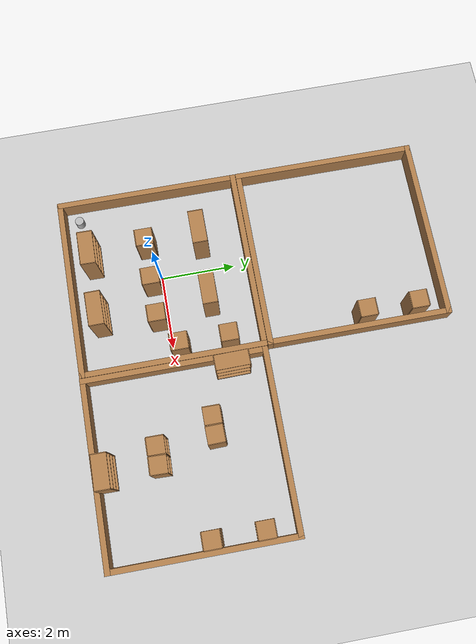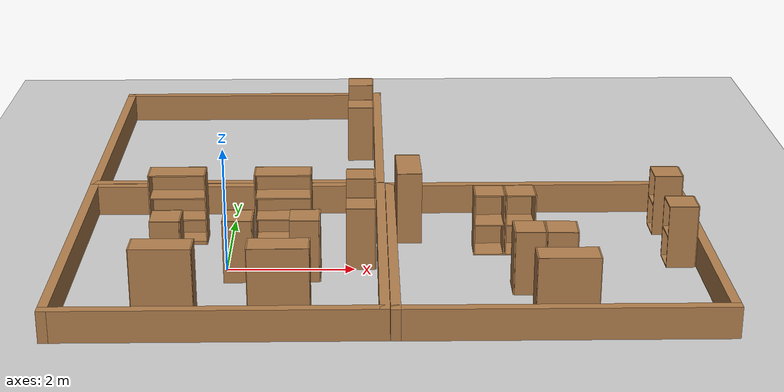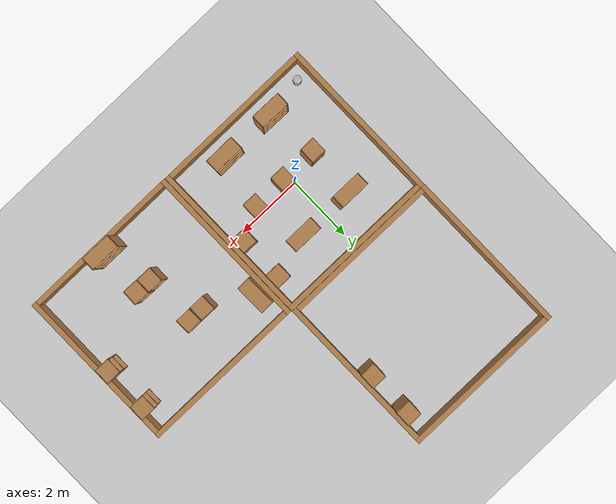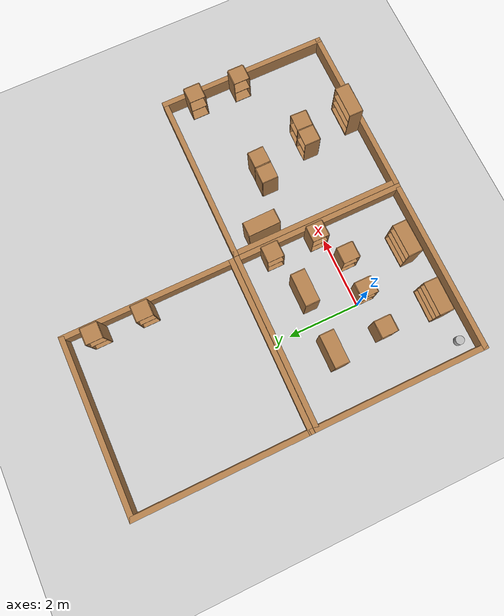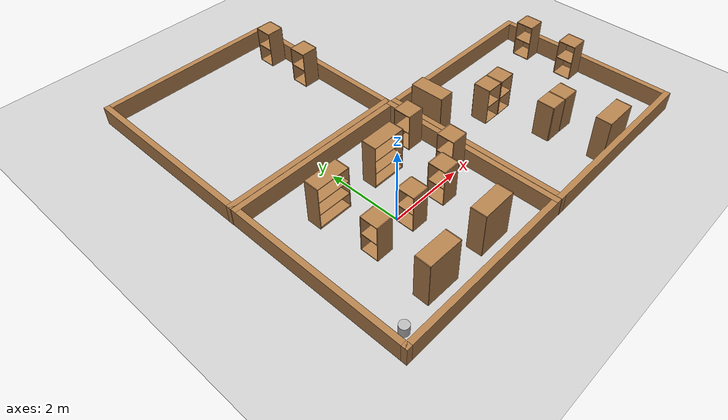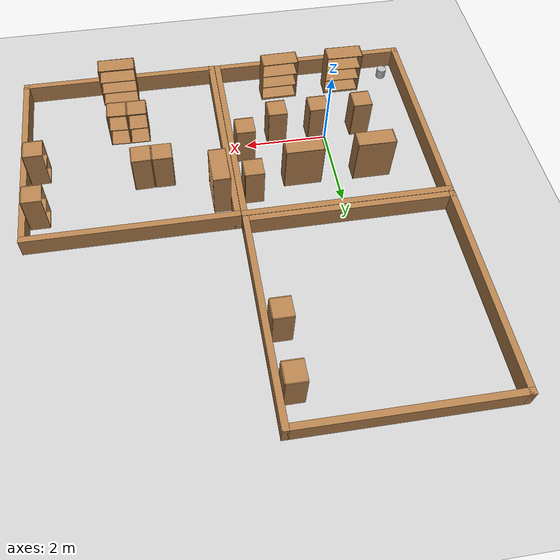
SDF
<sdf version="1.7">
 <world name="default">
  <model name="ground_plane">
   <static>1</static>
   <link name="link">
    <collision name="collision">
     <geometry><plane><normal>0 0 1</normal><size>100 100</size></plane></geometry>
     <surface><friction><ode><mu>100</mu><mu2>50</mu2></ode></friction></surface>
    </collision>
    <visual name="visual">
     <cast_shadows>0</cast_shadows>
     <geometry><plane><normal>0 0 1</normal><size>100 100</size></plane></geometry>
     <material>
      <script><uri>file://media/materials/scripts/gazebo.material</uri><name>Gazebo/Grey</name></script>
     </material>
    </visual>
   </link>
  </model>
  <light name="sun" type="directional">
   <pose>0 0 10 0 -0 0</pose>
   <diffuse>0.8 0.8 0.8 1</diffuse>
   <specular>0.2 0.2 0.2 1</specular>
   <attenuation>
    <range>1000</range>
    <constant>0.9</constant>
    <linear>0.01</linear>
    <quadratic>0.001</quadratic>
   </attenuation>
   <direction>-0.5 0.1 -0.9</direction>
   <spot><inner_angle>0</inner_angle><outer_angle>0</outer_angle><falloff>0</falloff></spot>
  </light>
  <scene><shadows>0</shadows><ambient>0.4 0.4 0.4 1</ambient><background>0.7 0.7 0.7 1</background></scene>
  <physics type="ode">
   <real_time_update_rate>1000</real_time_update_rate>
   <max_step_size>0.001</max_step_size>
   <real_time_factor>1</real_time_factor>
   <ode>
    <solver>
     <type>quick</type>
     <iters>150</iters>
     <precon_iters>0</precon_iters>
     <sor>1.4</sor>
     <use_dynamic_moi_rescaling>1</use_dynamic_moi_rescaling>
    </solver>
    <constraints>
     <cfm>1e-05</cfm>
     <erp>0.2</erp>
     <contact_max_correcting_vel>2000</contact_max_correcting_vel>
     <contact_surface_layer>0.01</contact_surface_layer>
    </constraints>
   </ode>
  </physics>
  <model name="turtlebot3_dqn_world">
   <pose>0.00548 -0.006455 0 0 -0 0</pose>
   <static>1</static>
   <frame name="turtlebot3_square::__model__" attached_to="turtlebot3_square::Wall_1">
    <pose relative_to="__model__">0 0 0 0 -0 0</pose>
   </frame>
   <link name="turtlebot3_square::Wall_1">
    <collision name="Wall_1_Collision">
     <geometry><box><size>5 0.15 0.5</size></box></geometry>
     <pose>0 0 0.25 0 -0 0</pose>
    </collision>
    <visual name="Wall_1_Visual">
     <pose>0 0 0.25 0 -0 0</pose>
     <geometry><box><size>5 0.15 0.5</size></box></geometry>
     <material>
      <script><uri>file://media/materials/scripts/gazebo.material</uri><name>Gazebo/Wood</name></script>
      <ambient>1 1 1 1</ambient>
     </material>
    </visual>
    <pose relative_to="turtlebot3_square::__model__">-2.425 0 0 0 -0 1.5708</pose>
   </link>
   <link name="turtlebot3_square::Wall_2">
    <collision name="Wall_2_Collision">
     <geometry><box><size>5 0.15 0.5</size></box></geometry>
     <pose>0 0 0.25 0 -0 0</pose>
    </collision>
    <visual name="Wall_2_Visual">
     <pose>0 0 0.25 0 -0 0</pose>
     <geometry><box><size>5 0.15 0.5</size></box></geometry>
     <material>
      <script><uri>file://media/materials/scripts/gazebo.material</uri><name>Gazebo/Wood</name></script>
      <ambient>1 1 1 1</ambient>
     </material>
    </visual>
    <pose relative_to="turtlebot3_square::__model__">0 2.425 0 0 -0 0</pose>
   </link>
   <link name="turtlebot3_square::Wall_3">
    <collision name="Wall_3_Collision">
     <geometry><box><size>5 0.15 0.5</size></box></geometry>
     <pose>0 0 0.25 0 -0 0</pose>
    </collision>
    <visual name="Wall_3_Visual">
     <pose>0 0 0.25 0 -0 0</pose>
     <geometry><box><size>5 0.15 0.5</size></box></geometry>
     <material>
      <script><uri>file://media/materials/scripts/gazebo.material</uri><name>Gazebo/Wood</name></script>
      <ambient>1 1 1 1</ambient>
     </material>
    </visual>
    <pose relative_to="turtlebot3_square::__model__">2.425 0 0 0 0 -1.5708</pose>
   </link>
   <link name="turtlebot3_square::Wall_4">
    <collision name="Wall_4_Collision">
     <geometry><box><size>5 0.15 0.5</size></box></geometry>
     <pose>0 0 0.25 0 -0 0</pose>
    </collision>
    <visual name="Wall_4_Visual">
     <pose>0 0 0.25 0 -0 0</pose>
     <geometry><box><size>5 0.15 0.5</size></box></geometry>
     <material>
      <script><uri>file://media/materials/scripts/gazebo.material</uri><name>Gazebo/Wood</name></script>
      <ambient>1 1 1 1</ambient>
     </material>
    </visual>
    <pose relative_to="turtlebot3_square::__model__">0 -2.425 0 0 -0 3.14159</pose>
   </link>
   <static>1</static>
  </model>
  <model name="turtlebot3_dqn_obstacle2">
   <pose>-0 0 0.124991 0 -0 0</pose>
   <plugin name="obstacle2" filename="libobstacle2.so"/>
   <frame name="obstacle2::__model__" attached_to="obstacle2::link">
    <pose relative_to="__model__">-2 -2 0 0 -0 0</pose>
   </frame>
   <link name="obstacle2::link">
    <collision name="collision">
     <geometry><cylinder><radius>0.12</radius><length>0.25</length></cylinder></geometry>
    </collision>
    <visual name="visual">
     <geometry><cylinder><radius>0.12</radius><length>0.25</length></cylinder></geometry>
    </visual>
    <pose relative_to="obstacle2::__model__">0 0 0 0 -0 0</pose>
    <inertial>
     <inertia><ixx>1</ixx><ixy>0</ixy><ixz>0</ixz><iyy>1</iyy><iyz>0</iyz><izz>1</izz></inertia>
     <mass>1</mass>
    </inertial>
   </link>
  </model>
  <model name="turtlebot3_dqn_world2">
   <static>1</static>
   <frame name="turtlebot3_square::__model__" attached_to="turtlebot3_square::Wall_1">
    <pose relative_to="__model__">0 5 0 0 -0 0</pose>
   </frame>
   <link name="turtlebot3_square::Wall_1">
    <collision name="Wall_1_Collision">
     <geometry><box><size>5 0.15 0.5</size></box></geometry>
     <pose>0 0 0.25 0 -0 0</pose>
    </collision>
    <visual name="Wall_1_Visual">
     <pose>0 0 0.25 0 -0 0</pose>
     <geometry><box><size>5 0.15 0.5</size></box></geometry>
     <material>
      <script><uri>file://media/materials/scripts/gazebo.material</uri><name>Gazebo/Wood</name></script>
      <ambient>1 1 1 1</ambient>
     </material>
    </visual>
    <pose relative_to="turtlebot3_square::__model__">-2.425 0 0 0 -0 1.5708</pose>
   </link>
   <link name="turtlebot3_square::Wall_2">
    <collision name="Wall_2_Collision">
     <geometry><box><size>5 0.15 0.5</size></box></geometry>
     <pose>0 0 0.25 0 -0 0</pose>
    </collision>
    <visual name="Wall_2_Visual">
     <pose>0 0 0.25 0 -0 0</pose>
     <geometry><box><size>5 0.15 0.5</size></box></geometry>
     <material>
      <script><uri>file://media/materials/scripts/gazebo.material</uri><name>Gazebo/Wood</name></script>
      <ambient>1 1 1 1</ambient>
     </material>
    </visual>
    <pose relative_to="turtlebot3_square::__model__">0 2.425 0 0 -0 0</pose>
   </link>
   <link name="turtlebot3_square::Wall_3">
    <collision name="Wall_3_Collision">
     <geometry><box><size>5 0.15 0.5</size></box></geometry>
     <pose>0 0 0.25 0 -0 0</pose>
    </collision>
    <visual name="Wall_3_Visual">
     <pose>0 0 0.25 0 -0 0</pose>
     <geometry><box><size>5 0.15 0.5</size></box></geometry>
     <material>
      <script><uri>file://media/materials/scripts/gazebo.material</uri><name>Gazebo/Wood</name></script>
      <ambient>1 1 1 1</ambient>
     </material>
    </visual>
    <pose relative_to="turtlebot3_square::__model__">2.425 0 0 0 0 -1.5708</pose>
   </link>
   <link name="turtlebot3_square::Wall_4">
    <collision name="Wall_4_Collision">
     <geometry><box><size>5 0.15 0.5</size></box></geometry>
     <pose>0 0 0.25 0 -0 0</pose>
    </collision>
    <visual name="Wall_4_Visual">
     <pose>0 0 0.25 0 -0 0</pose>
     <geometry><box><size>5 0.15 0.5</size></box></geometry>
     <material>
      <script><uri>file://media/materials/scripts/gazebo.material</uri><name>Gazebo/Wood</name></script>
      <ambient>1 1 1 1</ambient>
     </material>
    </visual>
    <pose relative_to="turtlebot3_square::__model__">0 -2.425 0 0 -0 3.14159</pose>
   </link>
   <static>1</static>
  </model>
  <gravity>0 0 -9.8</gravity>
  <magnetic_field>6e-06 2.3e-05 -4.2e-05</magnetic_field>
  <atmosphere type="adiabatic"/>
  <audio><device>default</device></audio>
  <spherical_coordinates>
   <surface_model>EARTH_WGS84</surface_model>
   <latitude_deg>0</latitude_deg>
   <longitude_deg>0</longitude_deg>
   <elevation>0</elevation>
   <heading_deg>0</heading_deg>
  </spherical_coordinates>
  <model name="cabinet">
   <static>1</static>
   <link name="cabinet_bottom_plate">
    <inertial>
     <pose>0 0 -1 0 -0 0</pose>
     <inertia><ixx>2.05</ixx><ixy>0</ixy><ixz>0</ixz><iyy>2.05</iyy><iyz>0</iyz><izz>2.05</izz></inertia>
     <mass>25</mass>
    </inertial>
    <collision name="cabinet_bottom_plate_geom">
     <pose>0 0 0.01 0 -0 0</pose>
     <geometry><box><size>0.45 0.45 0.02</size></box></geometry>
    </collision>
    <visual name="cabinet_bottom_plate_geom_visual">
     <pose>0 0 0.01 0 -0 0</pose>
     <geometry><box><size>0.45 0.45 0.02</size></box></geometry>
     <material>
      <script><uri>file://media/materials/scripts/gazebo.material</uri><name>Gazebo/Wood</name></script>
     </material>
    </visual>
    <collision name="cabinet_bottom_plate_geom_cabinet_back_plate">
     <pose>0.235 0 0.51 0 -0 0</pose>
     <geometry><box><size>0.02 0.45 1.02</size></box></geometry>
    </collision>
    <visual name="cabinet_bottom_plate_geom_cabinet_back_plate_visual">
     <pose>0.235 0 0.51 0 -0 0</pose>
     <geometry><box><size>0.02 0.45 1.02</size></box></geometry>
     <material>
      <script><uri>file://media/materials/scripts/gazebo.material</uri><name>Gazebo/Wood</name></script>
     </material>
    </visual>
    <collision name="cabinet_bottom_plate_geom_cabinet_left_plate">
     <pose>0 0.235 0.51 0 -0 0</pose>
     <geometry><box><size>0.45 0.02 1.02</size></box></geometry>
    </collision>
    <visual name="cabinet_bottom_plate_geom_cabinet_left_plate_visual">
     <pose>0 0.235 0.51 0 -0 0</pose>
     <geometry><box><size>0.45 0.02 1.02</size></box></geometry>
     <material>
      <script><uri>file://media/materials/scripts/gazebo.material</uri><name>Gazebo/Wood</name></script>
     </material>
    </visual>
    <collision name="cabinet_bottom_plate_geom_cabinet_middle_plate">
     <pose>0 0 0.51 0 -0 0</pose>
     <geometry><box><size>0.45 0.45 0.02</size></box></geometry>
    </collision>
    <visual name="cabinet_bottom_plate_geom_cabinet_middle_plate_visual">
     <pose>0 0 0.51 0 -0 0</pose>
     <geometry><box><size>0.45 0.45 0.02</size></box></geometry>
     <material>
      <script><uri>file://media/materials/scripts/gazebo.material</uri><name>Gazebo/Wood</name></script>
     </material>
    </visual>
    <collision name="cabinet_bottom_plate_geom_cabinet_right_plate">
     <pose>0 -0.235 0.51 0 -0 0</pose>
     <geometry><box><size>0.45 0.02 1.02</size></box></geometry>
    </collision>
    <visual name="cabinet_bottom_plate_geom_cabinet_right_plate_visual">
     <pose>0 -0.235 0.51 0 -0 0</pose>
     <geometry><box><size>0.45 0.02 1.02</size></box></geometry>
     <material>
      <script><uri>file://media/materials/scripts/gazebo.material</uri><name>Gazebo/Wood</name></script>
     </material>
    </visual>
    <collision name="cabinet_bottom_plate_geom_cabinet_top_plate">
     <pose>0 0 1.01 0 -0 0</pose>
     <geometry><box><size>0.45 0.45 0.02</size></box></geometry>
    </collision>
    <visual name="cabinet_bottom_plate_geom_cabinet_top_plate_visual">
     <pose>0 0 1.01 0 -0 0</pose>
     <geometry><box><size>0.45 0.45 0.02</size></box></geometry>
     <material>
      <script><uri>file://media/materials/scripts/gazebo.material</uri><name>Gazebo/Wood</name></script>
     </material>
    </visual>
   </link>
   <pose>2.09193 0.230267 0 0 -0 0</pose>
  </model>
  <model name="cabinet_0">
   <static>1</static>
   <link name="cabinet_bottom_plate">
    <inertial>
     <pose>0 0 -1 0 -0 0</pose>
     <inertia><ixx>2.05</ixx><ixy>0</ixy><ixz>0</ixz><iyy>2.05</iyy><iyz>0</iyz><izz>2.05</izz></inertia>
     <mass>25</mass>
    </inertial>
    <collision name="cabinet_bottom_plate_geom">
     <pose>0 0 0.01 0 -0 0</pose>
     <geometry><box><size>0.45 0.45 0.02</size></box></geometry>
    </collision>
    <visual name="cabinet_bottom_plate_geom_visual">
     <pose>0 0 0.01 0 -0 0</pose>
     <geometry><box><size>0.45 0.45 0.02</size></box></geometry>
     <material>
      <script><uri>file://media/materials/scripts/gazebo.material</uri><name>Gazebo/Wood</name></script>
     </material>
    </visual>
    <collision name="cabinet_bottom_plate_geom_cabinet_back_plate">
     <pose>0.235 0 0.51 0 -0 0</pose>
     <geometry><box><size>0.02 0.45 1.02</size></box></geometry>
    </collision>
    <visual name="cabinet_bottom_plate_geom_cabinet_back_plate_visual">
     <pose>0.235 0 0.51 0 -0 0</pose>
     <geometry><box><size>0.02 0.45 1.02</size></box></geometry>
     <material>
      <script><uri>file://media/materials/scripts/gazebo.material</uri><name>Gazebo/Wood</name></script>
     </material>
    </visual>
    <collision name="cabinet_bottom_plate_geom_cabinet_left_plate">
     <pose>0 0.235 0.51 0 -0 0</pose>
     <geometry><box><size>0.45 0.02 1.02</size></box></geometry>
    </collision>
    <visual name="cabinet_bottom_plate_geom_cabinet_left_plate_visual">
     <pose>0 0.235 0.51 0 -0 0</pose>
     <geometry><box><size>0.45 0.02 1.02</size></box></geometry>
     <material>
      <script><uri>file://media/materials/scripts/gazebo.material</uri><name>Gazebo/Wood</name></script>
     </material>
    </visual>
    <collision name="cabinet_bottom_plate_geom_cabinet_middle_plate">
     <pose>0 0 0.51 0 -0 0</pose>
     <geometry><box><size>0.45 0.45 0.02</size></box></geometry>
    </collision>
    <visual name="cabinet_bottom_plate_geom_cabinet_middle_plate_visual">
     <pose>0 0 0.51 0 -0 0</pose>
     <geometry><box><size>0.45 0.45 0.02</size></box></geometry>
     <material>
      <script><uri>file://media/materials/scripts/gazebo.material</uri><name>Gazebo/Wood</name></script>
     </material>
    </visual>
    <collision name="cabinet_bottom_plate_geom_cabinet_right_plate">
     <pose>0 -0.235 0.51 0 -0 0</pose>
     <geometry><box><size>0.45 0.02 1.02</size></box></geometry>
    </collision>
    <visual name="cabinet_bottom_plate_geom_cabinet_right_plate_visual">
     <pose>0 -0.235 0.51 0 -0 0</pose>
     <geometry><box><size>0.45 0.02 1.02</size></box></geometry>
     <material>
      <script><uri>file://media/materials/scripts/gazebo.material</uri><name>Gazebo/Wood</name></script>
     </material>
    </visual>
    <collision name="cabinet_bottom_plate_geom_cabinet_top_plate">
     <pose>0 0 1.01 0 -0 0</pose>
     <geometry><box><size>0.45 0.45 0.02</size></box></geometry>
    </collision>
    <visual name="cabinet_bottom_plate_geom_cabinet_top_plate_visual">
     <pose>0 0 1.01 0 -0 0</pose>
     <geometry><box><size>0.45 0.45 0.02</size></box></geometry>
     <material>
      <script><uri>file://media/materials/scripts/gazebo.material</uri><name>Gazebo/Wood</name></script>
     </material>
    </visual>
   </link>
   <pose>2.08844 1.53729 0 0 -0 0</pose>
  </model>
  <model name="bookshelf">
   <static>1</static>
   <link name="link">
    <inertial><mass>1</mass></inertial>
    <collision name="back">
     <pose>0 0.005 0.6 0 -0 0</pose>
     <geometry><box><size>0.9 0.01 1.2</size></box></geometry>
    </collision>
    <visual name="visual1">
     <pose>0 0.005 0.6 0 -0 0</pose>
     <geometry><box><size>0.9 0.01 1.2</size></box></geometry>
     <material>
      <script><uri>file://media/materials/scripts/gazebo.material</uri><name>Gazebo/Wood</name></script>
     </material>
    </visual>
    <collision name="left_side">
     <pose>0.45 -0.195 0.6 0 -0 0</pose>
     <geometry><box><size>0.02 0.4 1.2</size></box></geometry>
    </collision>
    <visual name="visual2">
     <pose>0.45 -0.195 0.6 0 -0 0</pose>
     <geometry><box><size>0.02 0.4 1.2</size></box></geometry>
     <material>
      <script><uri>file://media/materials/scripts/gazebo.material</uri><name>Gazebo/Wood</name></script>
     </material>
    </visual>
    <collision name="right_side">
     <pose>-0.45 -0.195 0.6 0 -0 0</pose>
     <geometry><box><size>0.02 0.4 1.2</size></box></geometry>
    </collision>
    <visual name="visual3">
     <pose>-0.45 -0.195 0.6 0 -0 0</pose>
     <geometry><box><size>0.02 0.4 1.2</size></box></geometry>
     <material>
      <script><uri>file://media/materials/scripts/gazebo.material</uri><name>Gazebo/Wood</name></script>
     </material>
    </visual>
    <collision name="bottom">
     <pose>0 -0.195 0.03 0 -0 0</pose>
     <geometry><box><size>0.88 0.4 0.06</size></box></geometry>
    </collision>
    <visual name="visual4">
     <pose>0 -0.195 0.03 0 -0 0</pose>
     <geometry><box><size>0.88 0.4 0.06</size></box></geometry>
     <material>
      <script><uri>file://media/materials/scripts/gazebo.material</uri><name>Gazebo/Wood</name></script>
     </material>
    </visual>
    <collision name="top">
     <pose>0 -0.195 1.19 0 -0 0</pose>
     <geometry><box><size>0.88 0.4 0.02</size></box></geometry>
    </collision>
    <visual name="visual5">
     <pose>0 -0.195 1.19 0 -0 0</pose>
     <geometry><box><size>0.88 0.4 0.02</size></box></geometry>
     <material>
      <script><uri>file://media/materials/scripts/gazebo.material</uri><name>Gazebo/Wood</name></script>
     </material>
    </visual>
    <collision name="low_shelf">
     <pose>0 -0.195 0.43 0 -0 0</pose>
     <geometry><box><size>0.88 0.4 0.02</size></box></geometry>
    </collision>
    <visual name="visual6">
     <pose>0 -0.195 0.43 0 -0 0</pose>
     <geometry><box><size>0.88 0.4 0.02</size></box></geometry>
     <material>
      <script><uri>file://media/materials/scripts/gazebo.material</uri><name>Gazebo/Wood</name></script>
     </material>
    </visual>
    <collision name="high_shelf">
     <pose>0 -0.195 0.8 0 -0 0</pose>
     <geometry><box><size>0.88 0.4 0.02</size></box></geometry>
    </collision>
    <visual name="visual7">
     <pose>0 -0.195 0.8 0 -0 0</pose>
     <geometry><box><size>0.88 0.4 0.02</size></box></geometry>
     <material>
      <script><uri>file://media/materials/scripts/gazebo.material</uri><name>Gazebo/Wood</name></script>
     </material>
    </visual>
   </link>
   <pose>0.848772 1.39903 0 0 -0 0</pose>
  </model>
  <model name="bookshelf_0">
   <static>1</static>
   <link name="link">
    <inertial><mass>1</mass></inertial>
    <collision name="back">
     <pose>0 0.005 0.6 0 -0 0</pose>
     <geometry><box><size>0.9 0.01 1.2</size></box></geometry>
    </collision>
    <visual name="visual1">
     <pose>0 0.005 0.6 0 -0 0</pose>
     <geometry><box><size>0.9 0.01 1.2</size></box></geometry>
     <material>
      <script><uri>file://media/materials/scripts/gazebo.material</uri><name>Gazebo/Wood</name></script>
     </material>
    </visual>
    <collision name="left_side">
     <pose>0.45 -0.195 0.6 0 -0 0</pose>
     <geometry><box><size>0.02 0.4 1.2</size></box></geometry>
    </collision>
    <visual name="visual2">
     <pose>0.45 -0.195 0.6 0 -0 0</pose>
     <geometry><box><size>0.02 0.4 1.2</size></box></geometry>
     <material>
      <script><uri>file://media/materials/scripts/gazebo.material</uri><name>Gazebo/Wood</name></script>
     </material>
    </visual>
    <collision name="right_side">
     <pose>-0.45 -0.195 0.6 0 -0 0</pose>
     <geometry><box><size>0.02 0.4 1.2</size></box></geometry>
    </collision>
    <visual name="visual3">
     <pose>-0.45 -0.195 0.6 0 -0 0</pose>
     <geometry><box><size>0.02 0.4 1.2</size></box></geometry>
     <material>
      <script><uri>file://media/materials/scripts/gazebo.material</uri><name>Gazebo/Wood</name></script>
     </material>
    </visual>
    <collision name="bottom">
     <pose>0 -0.195 0.03 0 -0 0</pose>
     <geometry><box><size>0.88 0.4 0.06</size></box></geometry>
    </collision>
    <visual name="visual4">
     <pose>0 -0.195 0.03 0 -0 0</pose>
     <geometry><box><size>0.88 0.4 0.06</size></box></geometry>
     <material>
      <script><uri>file://media/materials/scripts/gazebo.material</uri><name>Gazebo/Wood</name></script>
     </material>
    </visual>
    <collision name="top">
     <pose>0 -0.195 1.19 0 -0 0</pose>
     <geometry><box><size>0.88 0.4 0.02</size></box></geometry>
    </collision>
    <visual name="visual5">
     <pose>0 -0.195 1.19 0 -0 0</pose>
     <geometry><box><size>0.88 0.4 0.02</size></box></geometry>
     <material>
      <script><uri>file://media/materials/scripts/gazebo.material</uri><name>Gazebo/Wood</name></script>
     </material>
    </visual>
    <collision name="low_shelf">
     <pose>0 -0.195 0.43 0 -0 0</pose>
     <geometry><box><size>0.88 0.4 0.02</size></box></geometry>
    </collision>
    <visual name="visual6">
     <pose>0 -0.195 0.43 0 -0 0</pose>
     <geometry><box><size>0.88 0.4 0.02</size></box></geometry>
     <material>
      <script><uri>file://media/materials/scripts/gazebo.material</uri><name>Gazebo/Wood</name></script>
     </material>
    </visual>
    <collision name="high_shelf">
     <pose>0 -0.195 0.8 0 -0 0</pose>
     <geometry><box><size>0.88 0.4 0.02</size></box></geometry>
    </collision>
    <visual name="visual7">
     <pose>0 -0.195 0.8 0 -0 0</pose>
     <geometry><box><size>0.88 0.4 0.02</size></box></geometry>
     <material>
      <script><uri>file://media/materials/scripts/gazebo.material</uri><name>Gazebo/Wood</name></script>
     </material>
    </visual>
   </link>
   <pose>-0.849551 1.4123 0 0 -0 0</pose>
  </model>
  <model name="cabinet_1">
   <static>1</static>
   <link name="cabinet_bottom_plate">
    <inertial>
     <pose>0 0 -1 0 -0 0</pose>
     <inertia><ixx>2.05</ixx><ixy>0</ixy><ixz>0</ixz><iyy>2.05</iyy><iyz>0</iyz><izz>2.05</izz></inertia>
     <mass>25</mass>
    </inertial>
    <collision name="cabinet_bottom_plate_geom">
     <pose>0 0 0.01 0 -0 0</pose>
     <geometry><box><size>0.45 0.45 0.02</size></box></geometry>
    </collision>
    <visual name="cabinet_bottom_plate_geom_visual">
     <pose>0 0 0.01 0 -0 0</pose>
     <geometry><box><size>0.45 0.45 0.02</size></box></geometry>
     <material>
      <script><uri>file://media/materials/scripts/gazebo.material</uri><name>Gazebo/Wood</name></script>
     </material>
    </visual>
    <collision name="cabinet_bottom_plate_geom_cabinet_back_plate">
     <pose>0.235 0 0.51 0 -0 0</pose>
     <geometry><box><size>0.02 0.45 1.02</size></box></geometry>
    </collision>
    <visual name="cabinet_bottom_plate_geom_cabinet_back_plate_visual">
     <pose>0.235 0 0.51 0 -0 0</pose>
     <geometry><box><size>0.02 0.45 1.02</size></box></geometry>
     <material>
      <script><uri>file://media/materials/scripts/gazebo.material</uri><name>Gazebo/Wood</name></script>
     </material>
    </visual>
    <collision name="cabinet_bottom_plate_geom_cabinet_left_plate">
     <pose>0 0.235 0.51 0 -0 0</pose>
     <geometry><box><size>0.45 0.02 1.02</size></box></geometry>
    </collision>
    <visual name="cabinet_bottom_plate_geom_cabinet_left_plate_visual">
     <pose>0 0.235 0.51 0 -0 0</pose>
     <geometry><box><size>0.45 0.02 1.02</size></box></geometry>
     <material>
      <script><uri>file://media/materials/scripts/gazebo.material</uri><name>Gazebo/Wood</name></script>
     </material>
    </visual>
    <collision name="cabinet_bottom_plate_geom_cabinet_middle_plate">
     <pose>0 0 0.51 0 -0 0</pose>
     <geometry><box><size>0.45 0.45 0.02</size></box></geometry>
    </collision>
    <visual name="cabinet_bottom_plate_geom_cabinet_middle_plate_visual">
     <pose>0 0 0.51 0 -0 0</pose>
     <geometry><box><size>0.45 0.45 0.02</size></box></geometry>
     <material>
      <script><uri>file://media/materials/scripts/gazebo.material</uri><name>Gazebo/Wood</name></script>
     </material>
    </visual>
    <collision name="cabinet_bottom_plate_geom_cabinet_right_plate">
     <pose>0 -0.235 0.51 0 -0 0</pose>
     <geometry><box><size>0.45 0.02 1.02</size></box></geometry>
    </collision>
    <visual name="cabinet_bottom_plate_geom_cabinet_right_plate_visual">
     <pose>0 -0.235 0.51 0 -0 0</pose>
     <geometry><box><size>0.45 0.02 1.02</size></box></geometry>
     <material>
      <script><uri>file://media/materials/scripts/gazebo.material</uri><name>Gazebo/Wood</name></script>
     </material>
    </visual>
    <collision name="cabinet_bottom_plate_geom_cabinet_top_plate">
     <pose>0 0 1.01 0 -0 0</pose>
     <geometry><box><size>0.45 0.45 0.02</size></box></geometry>
    </collision>
    <visual name="cabinet_bottom_plate_geom_cabinet_top_plate_visual">
     <pose>0 0 1.01 0 -0 0</pose>
     <geometry><box><size>0.45 0.45 0.02</size></box></geometry>
     <material>
      <script><uri>file://media/materials/scripts/gazebo.material</uri><name>Gazebo/Wood</name></script>
     </material>
    </visual>
   </link>
   <pose>1.23211 -0.234998 0 0 -0 0</pose>
  </model>
  <model name="cabinet_2">
   <static>1</static>
   <link name="cabinet_bottom_plate">
    <inertial>
     <pose>0 0 -1 0 -0 0</pose>
     <inertia><ixx>2.05</ixx><ixy>0</ixy><ixz>0</ixz><iyy>2.05</iyy><iyz>0</iyz><izz>2.05</izz></inertia>
     <mass>25</mass>
    </inertial>
    <collision name="cabinet_bottom_plate_geom">
     <pose>0 0 0.01 0 -0 0</pose>
     <geometry><box><size>0.45 0.45 0.02</size></box></geometry>
    </collision>
    <visual name="cabinet_bottom_plate_geom_visual">
     <pose>0 0 0.01 0 -0 0</pose>
     <geometry><box><size>0.45 0.45 0.02</size></box></geometry>
     <material>
      <script><uri>file://media/materials/scripts/gazebo.material</uri><name>Gazebo/Wood</name></script>
     </material>
    </visual>
    <collision name="cabinet_bottom_plate_geom_cabinet_back_plate">
     <pose>0.235 0 0.51 0 -0 0</pose>
     <geometry><box><size>0.02 0.45 1.02</size></box></geometry>
    </collision>
    <visual name="cabinet_bottom_plate_geom_cabinet_back_plate_visual">
     <pose>0.235 0 0.51 0 -0 0</pose>
     <geometry><box><size>0.02 0.45 1.02</size></box></geometry>
     <material>
      <script><uri>file://media/materials/scripts/gazebo.material</uri><name>Gazebo/Wood</name></script>
     </material>
    </visual>
    <collision name="cabinet_bottom_plate_geom_cabinet_left_plate">
     <pose>0 0.235 0.51 0 -0 0</pose>
     <geometry><box><size>0.45 0.02 1.02</size></box></geometry>
    </collision>
    <visual name="cabinet_bottom_plate_geom_cabinet_left_plate_visual">
     <pose>0 0.235 0.51 0 -0 0</pose>
     <geometry><box><size>0.45 0.02 1.02</size></box></geometry>
     <material>
      <script><uri>file://media/materials/scripts/gazebo.material</uri><name>Gazebo/Wood</name></script>
     </material>
    </visual>
    <collision name="cabinet_bottom_plate_geom_cabinet_middle_plate">
     <pose>0 0 0.51 0 -0 0</pose>
     <geometry><box><size>0.45 0.45 0.02</size></box></geometry>
    </collision>
    <visual name="cabinet_bottom_plate_geom_cabinet_middle_plate_visual">
     <pose>0 0 0.51 0 -0 0</pose>
     <geometry><box><size>0.45 0.45 0.02</size></box></geometry>
     <material>
      <script><uri>file://media/materials/scripts/gazebo.material</uri><name>Gazebo/Wood</name></script>
     </material>
    </visual>
    <collision name="cabinet_bottom_plate_geom_cabinet_right_plate">
     <pose>0 -0.235 0.51 0 -0 0</pose>
     <geometry><box><size>0.45 0.02 1.02</size></box></geometry>
    </collision>
    <visual name="cabinet_bottom_plate_geom_cabinet_right_plate_visual">
     <pose>0 -0.235 0.51 0 -0 0</pose>
     <geometry><box><size>0.45 0.02 1.02</size></box></geometry>
     <material>
      <script><uri>file://media/materials/scripts/gazebo.material</uri><name>Gazebo/Wood</name></script>
     </material>
    </visual>
    <collision name="cabinet_bottom_plate_geom_cabinet_top_plate">
     <pose>0 0 1.01 0 -0 0</pose>
     <geometry><box><size>0.45 0.45 0.02</size></box></geometry>
    </collision>
    <visual name="cabinet_bottom_plate_geom_cabinet_top_plate_visual">
     <pose>0 0 1.01 0 -0 0</pose>
     <geometry><box><size>0.45 0.45 0.02</size></box></geometry>
     <material>
      <script><uri>file://media/materials/scripts/gazebo.material</uri><name>Gazebo/Wood</name></script>
     </material>
    </visual>
   </link>
   <pose>0.209044 -0.240001 0 0 -0 0</pose>
  </model>
  <model name="cabinet_3">
   <static>1</static>
   <link name="cabinet_bottom_plate">
    <inertial>
     <pose>0 0 -1 0 -0 0</pose>
     <inertia><ixx>2.05</ixx><ixy>0</ixy><ixz>0</ixz><iyy>2.05</iyy><iyz>0</iyz><izz>2.05</izz></inertia>
     <mass>25</mass>
    </inertial>
    <collision name="cabinet_bottom_plate_geom">
     <pose>0 0 0.01 0 -0 0</pose>
     <geometry><box><size>0.45 0.45 0.02</size></box></geometry>
    </collision>
    <visual name="cabinet_bottom_plate_geom_visual">
     <pose>0 0 0.01 0 -0 0</pose>
     <geometry><box><size>0.45 0.45 0.02</size></box></geometry>
     <material>
      <script><uri>file://media/materials/scripts/gazebo.material</uri><name>Gazebo/Wood</name></script>
     </material>
    </visual>
    <collision name="cabinet_bottom_plate_geom_cabinet_back_plate">
     <pose>0.235 0 0.51 0 -0 0</pose>
     <geometry><box><size>0.02 0.45 1.02</size></box></geometry>
    </collision>
    <visual name="cabinet_bottom_plate_geom_cabinet_back_plate_visual">
     <pose>0.235 0 0.51 0 -0 0</pose>
     <geometry><box><size>0.02 0.45 1.02</size></box></geometry>
     <material>
      <script><uri>file://media/materials/scripts/gazebo.material</uri><name>Gazebo/Wood</name></script>
     </material>
    </visual>
    <collision name="cabinet_bottom_plate_geom_cabinet_left_plate">
     <pose>0 0.235 0.51 0 -0 0</pose>
     <geometry><box><size>0.45 0.02 1.02</size></box></geometry>
    </collision>
    <visual name="cabinet_bottom_plate_geom_cabinet_left_plate_visual">
     <pose>0 0.235 0.51 0 -0 0</pose>
     <geometry><box><size>0.45 0.02 1.02</size></box></geometry>
     <material>
      <script><uri>file://media/materials/scripts/gazebo.material</uri><name>Gazebo/Wood</name></script>
     </material>
    </visual>
    <collision name="cabinet_bottom_plate_geom_cabinet_middle_plate">
     <pose>0 0 0.51 0 -0 0</pose>
     <geometry><box><size>0.45 0.45 0.02</size></box></geometry>
    </collision>
    <visual name="cabinet_bottom_plate_geom_cabinet_middle_plate_visual">
     <pose>0 0 0.51 0 -0 0</pose>
     <geometry><box><size>0.45 0.45 0.02</size></box></geometry>
     <material>
      <script><uri>file://media/materials/scripts/gazebo.material</uri><name>Gazebo/Wood</name></script>
     </material>
    </visual>
    <collision name="cabinet_bottom_plate_geom_cabinet_right_plate">
     <pose>0 -0.235 0.51 0 -0 0</pose>
     <geometry><box><size>0.45 0.02 1.02</size></box></geometry>
    </collision>
    <visual name="cabinet_bottom_plate_geom_cabinet_right_plate_visual">
     <pose>0 -0.235 0.51 0 -0 0</pose>
     <geometry><box><size>0.45 0.02 1.02</size></box></geometry>
     <material>
      <script><uri>file://media/materials/scripts/gazebo.material</uri><name>Gazebo/Wood</name></script>
     </material>
    </visual>
    <collision name="cabinet_bottom_plate_geom_cabinet_top_plate">
     <pose>0 0 1.01 0 -0 0</pose>
     <geometry><box><size>0.45 0.45 0.02</size></box></geometry>
    </collision>
    <visual name="cabinet_bottom_plate_geom_cabinet_top_plate_visual">
     <pose>0 0 1.01 0 -0 0</pose>
     <geometry><box><size>0.45 0.45 0.02</size></box></geometry>
     <material>
      <script><uri>file://media/materials/scripts/gazebo.material</uri><name>Gazebo/Wood</name></script>
     </material>
    </visual>
   </link>
   <pose>-0.890122 -0.240947 0 0 -0 0</pose>
  </model>
  <model name="bookshelf_1">
   <static>1</static>
   <link name="link">
    <inertial><mass>1</mass></inertial>
    <collision name="back">
     <pose>0 0.005 0.6 0 -0 0</pose>
     <geometry><box><size>0.9 0.01 1.2</size></box></geometry>
    </collision>
    <visual name="visual1">
     <pose>0 0.005 0.6 0 -0 0</pose>
     <geometry><box><size>0.9 0.01 1.2</size></box></geometry>
     <material>
      <script><uri>file://media/materials/scripts/gazebo.material</uri><name>Gazebo/Wood</name></script>
     </material>
    </visual>
    <collision name="left_side">
     <pose>0.45 -0.195 0.6 0 -0 0</pose>
     <geometry><box><size>0.02 0.4 1.2</size></box></geometry>
    </collision>
    <visual name="visual2">
     <pose>0.45 -0.195 0.6 0 -0 0</pose>
     <geometry><box><size>0.02 0.4 1.2</size></box></geometry>
     <material>
      <script><uri>file://media/materials/scripts/gazebo.material</uri><name>Gazebo/Wood</name></script>
     </material>
    </visual>
    <collision name="right_side">
     <pose>-0.45 -0.195 0.6 0 -0 0</pose>
     <geometry><box><size>0.02 0.4 1.2</size></box></geometry>
    </collision>
    <visual name="visual3">
     <pose>-0.45 -0.195 0.6 0 -0 0</pose>
     <geometry><box><size>0.02 0.4 1.2</size></box></geometry>
     <material>
      <script><uri>file://media/materials/scripts/gazebo.material</uri><name>Gazebo/Wood</name></script>
     </material>
    </visual>
    <collision name="bottom">
     <pose>0 -0.195 0.03 0 -0 0</pose>
     <geometry><box><size>0.88 0.4 0.06</size></box></geometry>
    </collision>
    <visual name="visual4">
     <pose>0 -0.195 0.03 0 -0 0</pose>
     <geometry><box><size>0.88 0.4 0.06</size></box></geometry>
     <material>
      <script><uri>file://media/materials/scripts/gazebo.material</uri><name>Gazebo/Wood</name></script>
     </material>
    </visual>
    <collision name="top">
     <pose>0 -0.195 1.19 0 -0 0</pose>
     <geometry><box><size>0.88 0.4 0.02</size></box></geometry>
    </collision>
    <visual name="visual5">
     <pose>0 -0.195 1.19 0 -0 0</pose>
     <geometry><box><size>0.88 0.4 0.02</size></box></geometry>
     <material>
      <script><uri>file://media/materials/scripts/gazebo.material</uri><name>Gazebo/Wood</name></script>
     </material>
    </visual>
    <collision name="low_shelf">
     <pose>0 -0.195 0.43 0 -0 0</pose>
     <geometry><box><size>0.88 0.4 0.02</size></box></geometry>
    </collision>
    <visual name="visual6">
     <pose>0 -0.195 0.43 0 -0 0</pose>
     <geometry><box><size>0.88 0.4 0.02</size></box></geometry>
     <material>
      <script><uri>file://media/materials/scripts/gazebo.material</uri><name>Gazebo/Wood</name></script>
     </material>
    </visual>
    <collision name="high_shelf">
     <pose>0 -0.195 0.8 0 -0 0</pose>
     <geometry><box><size>0.88 0.4 0.02</size></box></geometry>
    </collision>
    <visual name="visual7">
     <pose>0 -0.195 0.8 0 -0 0</pose>
     <geometry><box><size>0.88 0.4 0.02</size></box></geometry>
     <material>
      <script><uri>file://media/materials/scripts/gazebo.material</uri><name>Gazebo/Wood</name></script>
     </material>
    </visual>
   </link>
   <pose>0.903255 -1.95742 0 0 0 -3.13284</pose>
  </model>
  <model name="bookshelf_2">
   <static>1</static>
   <link name="link">
    <inertial><mass>1</mass></inertial>
    <collision name="back">
     <pose>0 0.005 0.6 0 -0 0</pose>
     <geometry><box><size>0.9 0.01 1.2</size></box></geometry>
    </collision>
    <visual name="visual1">
     <pose>0 0.005 0.6 0 -0 0</pose>
     <geometry><box><size>0.9 0.01 1.2</size></box></geometry>
     <material>
      <script><uri>file://media/materials/scripts/gazebo.material</uri><name>Gazebo/Wood</name></script>
     </material>
    </visual>
    <collision name="left_side">
     <pose>0.45 -0.195 0.6 0 -0 0</pose>
     <geometry><box><size>0.02 0.4 1.2</size></box></geometry>
    </collision>
    <visual name="visual2">
     <pose>0.45 -0.195 0.6 0 -0 0</pose>
     <geometry><box><size>0.02 0.4 1.2</size></box></geometry>
     <material>
      <script><uri>file://media/materials/scripts/gazebo.material</uri><name>Gazebo/Wood</name></script>
     </material>
    </visual>
    <collision name="right_side">
     <pose>-0.45 -0.195 0.6 0 -0 0</pose>
     <geometry><box><size>0.02 0.4 1.2</size></box></geometry>
    </collision>
    <visual name="visual3">
     <pose>-0.45 -0.195 0.6 0 -0 0</pose>
     <geometry><box><size>0.02 0.4 1.2</size></box></geometry>
     <material>
      <script><uri>file://media/materials/scripts/gazebo.material</uri><name>Gazebo/Wood</name></script>
     </material>
    </visual>
    <collision name="bottom">
     <pose>0 -0.195 0.03 0 -0 0</pose>
     <geometry><box><size>0.88 0.4 0.06</size></box></geometry>
    </collision>
    <visual name="visual4">
     <pose>0 -0.195 0.03 0 -0 0</pose>
     <geometry><box><size>0.88 0.4 0.06</size></box></geometry>
     <material>
      <script><uri>file://media/materials/scripts/gazebo.material</uri><name>Gazebo/Wood</name></script>
     </material>
    </visual>
    <collision name="top">
     <pose>0 -0.195 1.19 0 -0 0</pose>
     <geometry><box><size>0.88 0.4 0.02</size></box></geometry>
    </collision>
    <visual name="visual5">
     <pose>0 -0.195 1.19 0 -0 0</pose>
     <geometry><box><size>0.88 0.4 0.02</size></box></geometry>
     <material>
      <script><uri>file://media/materials/scripts/gazebo.material</uri><name>Gazebo/Wood</name></script>
     </material>
    </visual>
    <collision name="low_shelf">
     <pose>0 -0.195 0.43 0 -0 0</pose>
     <geometry><box><size>0.88 0.4 0.02</size></box></geometry>
    </collision>
    <visual name="visual6">
     <pose>0 -0.195 0.43 0 -0 0</pose>
     <geometry><box><size>0.88 0.4 0.02</size></box></geometry>
     <material>
      <script><uri>file://media/materials/scripts/gazebo.material</uri><name>Gazebo/Wood</name></script>
     </material>
    </visual>
    <collision name="high_shelf">
     <pose>0 -0.195 0.8 0 -0 0</pose>
     <geometry><box><size>0.88 0.4 0.02</size></box></geometry>
    </collision>
    <visual name="visual7">
     <pose>0 -0.195 0.8 0 -0 0</pose>
     <geometry><box><size>0.88 0.4 0.02</size></box></geometry>
     <material>
      <script><uri>file://media/materials/scripts/gazebo.material</uri><name>Gazebo/Wood</name></script>
     </material>
    </visual>
   </link>
   <pose>-0.783777 -1.9532 0 0 -0 3.12951</pose>
  </model>
  <model name="cabinet_4">
   <static>1</static>
   <link name="cabinet_bottom_plate">
    <inertial>
     <pose>0 0 -1 0 -0 0</pose>
     <inertia><ixx>2.05</ixx><ixy>0</ixy><ixz>0</ixz><iyy>2.05</iyy><iyz>0</iyz><izz>2.05</izz></inertia>
     <mass>25</mass>
    </inertial>
    <collision name="cabinet_bottom_plate_geom">
     <pose>0 0 0.01 0 -0 0</pose>
     <geometry><box><size>0.45 0.45 0.02</size></box></geometry>
    </collision>
    <visual name="cabinet_bottom_plate_geom_visual">
     <pose>0 0 0.01 0 -0 0</pose>
     <geometry><box><size>0.45 0.45 0.02</size></box></geometry>
     <material>
      <script><uri>file://media/materials/scripts/gazebo.material</uri><name>Gazebo/Wood</name></script>
     </material>
    </visual>
    <collision name="cabinet_bottom_plate_geom_cabinet_back_plate">
     <pose>0.235 0 0.51 0 -0 0</pose>
     <geometry><box><size>0.02 0.45 1.02</size></box></geometry>
    </collision>
    <visual name="cabinet_bottom_plate_geom_cabinet_back_plate_visual">
     <pose>0.235 0 0.51 0 -0 0</pose>
     <geometry><box><size>0.02 0.45 1.02</size></box></geometry>
     <material>
      <script><uri>file://media/materials/scripts/gazebo.material</uri><name>Gazebo/Wood</name></script>
     </material>
    </visual>
    <collision name="cabinet_bottom_plate_geom_cabinet_left_plate">
     <pose>0 0.235 0.51 0 -0 0</pose>
     <geometry><box><size>0.45 0.02 1.02</size></box></geometry>
    </collision>
    <visual name="cabinet_bottom_plate_geom_cabinet_left_plate_visual">
     <pose>0 0.235 0.51 0 -0 0</pose>
     <geometry><box><size>0.45 0.02 1.02</size></box></geometry>
     <material>
      <script><uri>file://media/materials/scripts/gazebo.material</uri><name>Gazebo/Wood</name></script>
     </material>
    </visual>
    <collision name="cabinet_bottom_plate_geom_cabinet_middle_plate">
     <pose>0 0 0.51 0 -0 0</pose>
     <geometry><box><size>0.45 0.45 0.02</size></box></geometry>
    </collision>
    <visual name="cabinet_bottom_plate_geom_cabinet_middle_plate_visual">
     <pose>0 0 0.51 0 -0 0</pose>
     <geometry><box><size>0.45 0.45 0.02</size></box></geometry>
     <material>
      <script><uri>file://media/materials/scripts/gazebo.material</uri><name>Gazebo/Wood</name></script>
     </material>
    </visual>
    <collision name="cabinet_bottom_plate_geom_cabinet_right_plate">
     <pose>0 -0.235 0.51 0 -0 0</pose>
     <geometry><box><size>0.45 0.02 1.02</size></box></geometry>
    </collision>
    <visual name="cabinet_bottom_plate_geom_cabinet_right_plate_visual">
     <pose>0 -0.235 0.51 0 -0 0</pose>
     <geometry><box><size>0.45 0.02 1.02</size></box></geometry>
     <material>
      <script><uri>file://media/materials/scripts/gazebo.material</uri><name>Gazebo/Wood</name></script>
     </material>
    </visual>
    <collision name="cabinet_bottom_plate_geom_cabinet_top_plate">
     <pose>0 0 1.01 0 -0 0</pose>
     <geometry><box><size>0.45 0.45 0.02</size></box></geometry>
    </collision>
    <visual name="cabinet_bottom_plate_geom_cabinet_top_plate_visual">
     <pose>0 0 1.01 0 -0 0</pose>
     <geometry><box><size>0.45 0.45 0.02</size></box></geometry>
     <material>
      <script><uri>file://media/materials/scripts/gazebo.material</uri><name>Gazebo/Wood</name></script>
     </material>
    </visual>
   </link>
   <pose>2.10369 6.57114 0 0 -0 0</pose>
  </model>
  <model name="cabinet_5">
   <static>1</static>
   <link name="cabinet_bottom_plate">
    <inertial>
     <pose>0 0 -1 0 -0 0</pose>
     <inertia><ixx>2.05</ixx><ixy>0</ixy><ixz>0</ixz><iyy>2.05</iyy><iyz>0</iyz><izz>2.05</izz></inertia>
     <mass>25</mass>
    </inertial>
    <collision name="cabinet_bottom_plate_geom">
     <pose>0 0 0.01 0 -0 0</pose>
     <geometry><box><size>0.45 0.45 0.02</size></box></geometry>
    </collision>
    <visual name="cabinet_bottom_plate_geom_visual">
     <pose>0 0 0.01 0 -0 0</pose>
     <geometry><box><size>0.45 0.45 0.02</size></box></geometry>
     <material>
      <script><uri>file://media/materials/scripts/gazebo.material</uri><name>Gazebo/Wood</name></script>
     </material>
    </visual>
    <collision name="cabinet_bottom_plate_geom_cabinet_back_plate">
     <pose>0.235 0 0.51 0 -0 0</pose>
     <geometry><box><size>0.02 0.45 1.02</size></box></geometry>
    </collision>
    <visual name="cabinet_bottom_plate_geom_cabinet_back_plate_visual">
     <pose>0.235 0 0.51 0 -0 0</pose>
     <geometry><box><size>0.02 0.45 1.02</size></box></geometry>
     <material>
      <script><uri>file://media/materials/scripts/gazebo.material</uri><name>Gazebo/Wood</name></script>
     </material>
    </visual>
    <collision name="cabinet_bottom_plate_geom_cabinet_left_plate">
     <pose>0 0.235 0.51 0 -0 0</pose>
     <geometry><box><size>0.45 0.02 1.02</size></box></geometry>
    </collision>
    <visual name="cabinet_bottom_plate_geom_cabinet_left_plate_visual">
     <pose>0 0.235 0.51 0 -0 0</pose>
     <geometry><box><size>0.45 0.02 1.02</size></box></geometry>
     <material>
      <script><uri>file://media/materials/scripts/gazebo.material</uri><name>Gazebo/Wood</name></script>
     </material>
    </visual>
    <collision name="cabinet_bottom_plate_geom_cabinet_middle_plate">
     <pose>0 0 0.51 0 -0 0</pose>
     <geometry><box><size>0.45 0.45 0.02</size></box></geometry>
    </collision>
    <visual name="cabinet_bottom_plate_geom_cabinet_middle_plate_visual">
     <pose>0 0 0.51 0 -0 0</pose>
     <geometry><box><size>0.45 0.45 0.02</size></box></geometry>
     <material>
      <script><uri>file://media/materials/scripts/gazebo.material</uri><name>Gazebo/Wood</name></script>
     </material>
    </visual>
    <collision name="cabinet_bottom_plate_geom_cabinet_right_plate">
     <pose>0 -0.235 0.51 0 -0 0</pose>
     <geometry><box><size>0.45 0.02 1.02</size></box></geometry>
    </collision>
    <visual name="cabinet_bottom_plate_geom_cabinet_right_plate_visual">
     <pose>0 -0.235 0.51 0 -0 0</pose>
     <geometry><box><size>0.45 0.02 1.02</size></box></geometry>
     <material>
      <script><uri>file://media/materials/scripts/gazebo.material</uri><name>Gazebo/Wood</name></script>
     </material>
    </visual>
    <collision name="cabinet_bottom_plate_geom_cabinet_top_plate">
     <pose>0 0 1.01 0 -0 0</pose>
     <geometry><box><size>0.45 0.45 0.02</size></box></geometry>
    </collision>
    <visual name="cabinet_bottom_plate_geom_cabinet_top_plate_visual">
     <pose>0 0 1.01 0 -0 0</pose>
     <geometry><box><size>0.45 0.45 0.02</size></box></geometry>
     <material>
      <script><uri>file://media/materials/scripts/gazebo.material</uri><name>Gazebo/Wood</name></script>
     </material>
    </visual>
   </link>
   <pose>2.09564 5.20287 0 0 -0 0</pose>
  </model>
  <model name="turtlebot3_square">
   <pose>5.01138 -0.015749 0 0 -0 0</pose>
   <link name="Wall_1">
    <collision name="Wall_1_Collision">
     <geometry><box><size>5 0.15 0.5</size></box></geometry>
     <pose>0 0 0.25 0 -0 0</pose>
    </collision>
    <visual name="Wall_1_Visual">
     <pose>0 0 0.25 0 -0 0</pose>
     <geometry><box><size>5 0.15 0.5</size></box></geometry>
     <material>
      <script><uri>file://media/materials/scripts/gazebo.material</uri><name>Gazebo/Wood</name></script>
      <ambient>1 1 1 1</ambient>
     </material>
    </visual>
    <pose>-2.425 0 0 0 -0 1.5708</pose>
   </link>
   <link name="Wall_2">
    <collision name="Wall_2_Collision">
     <geometry><box><size>5 0.15 0.5</size></box></geometry>
     <pose>0 0 0.25 0 -0 0</pose>
    </collision>
    <visual name="Wall_2_Visual">
     <pose>0 0 0.25 0 -0 0</pose>
     <geometry><box><size>5 0.15 0.5</size></box></geometry>
     <material>
      <script><uri>file://media/materials/scripts/gazebo.material</uri><name>Gazebo/Wood</name></script>
      <ambient>1 1 1 1</ambient>
     </material>
    </visual>
    <pose>0 2.425 0 0 -0 0</pose>
   </link>
   <link name="Wall_3">
    <collision name="Wall_3_Collision">
     <geometry><box><size>5 0.15 0.5</size></box></geometry>
     <pose>0 0 0.25 0 -0 0</pose>
    </collision>
    <visual name="Wall_3_Visual">
     <pose>0 0 0.25 0 -0 0</pose>
     <geometry><box><size>5 0.15 0.5</size></box></geometry>
     <material>
      <script><uri>file://media/materials/scripts/gazebo.material</uri><name>Gazebo/Wood</name></script>
      <ambient>1 1 1 1</ambient>
     </material>
    </visual>
    <pose>2.425 0 0 0 0 -1.5708</pose>
   </link>
   <link name="Wall_4">
    <collision name="Wall_4_Collision">
     <geometry><box><size>5 0.15 0.5</size></box></geometry>
     <pose>0 0 0.25 0 -0 0</pose>
    </collision>
    <visual name="Wall_4_Visual">
     <pose>0 0 0.25 0 -0 0</pose>
     <geometry><box><size>5 0.15 0.5</size></box></geometry>
     <material>
      <script><uri>file://media/materials/scripts/gazebo.material</uri><name>Gazebo/Wood</name></script>
      <ambient>1 1 1 1</ambient>
     </material>
    </visual>
    <pose>0 -2.425 0 0 -0 3.14159</pose>
   </link>
   <static>1</static>
  </model>
  <model name="cabinet_6">
   <static>1</static>
   <link name="cabinet_bottom_plate">
    <inertial>
     <pose>0 0 -1 0 -0 0</pose>
     <inertia><ixx>2.05</ixx><ixy>0</ixy><ixz>0</ixz><iyy>2.05</iyy><iyz>0</iyz><izz>2.05</izz></inertia>
     <mass>25</mass>
    </inertial>
    <collision name="cabinet_bottom_plate_geom">
     <pose>0 0 0.01 0 -0 0</pose>
     <geometry><box><size>0.45 0.45 0.02</size></box></geometry>
    </collision>
    <visual name="cabinet_bottom_plate_geom_visual">
     <pose>0 0 0.01 0 -0 0</pose>
     <geometry><box><size>0.45 0.45 0.02</size></box></geometry>
     <material>
      <script><uri>file://media/materials/scripts/gazebo.material</uri><name>Gazebo/Wood</name></script>
     </material>
    </visual>
    <collision name="cabinet_bottom_plate_geom_cabinet_back_plate">
     <pose>0.235 0 0.51 0 -0 0</pose>
     <geometry><box><size>0.02 0.45 1.02</size></box></geometry>
    </collision>
    <visual name="cabinet_bottom_plate_geom_cabinet_back_plate_visual">
     <pose>0.235 0 0.51 0 -0 0</pose>
     <geometry><box><size>0.02 0.45 1.02</size></box></geometry>
     <material>
      <script><uri>file://media/materials/scripts/gazebo.material</uri><name>Gazebo/Wood</name></script>
     </material>
    </visual>
    <collision name="cabinet_bottom_plate_geom_cabinet_left_plate">
     <pose>0 0.235 0.51 0 -0 0</pose>
     <geometry><box><size>0.45 0.02 1.02</size></box></geometry>
    </collision>
    <visual name="cabinet_bottom_plate_geom_cabinet_left_plate_visual">
     <pose>0 0.235 0.51 0 -0 0</pose>
     <geometry><box><size>0.45 0.02 1.02</size></box></geometry>
     <material>
      <script><uri>file://media/materials/scripts/gazebo.material</uri><name>Gazebo/Wood</name></script>
     </material>
    </visual>
    <collision name="cabinet_bottom_plate_geom_cabinet_middle_plate">
     <pose>0 0 0.51 0 -0 0</pose>
     <geometry><box><size>0.45 0.45 0.02</size></box></geometry>
    </collision>
    <visual name="cabinet_bottom_plate_geom_cabinet_middle_plate_visual">
     <pose>0 0 0.51 0 -0 0</pose>
     <geometry><box><size>0.45 0.45 0.02</size></box></geometry>
     <material>
      <script><uri>file://media/materials/scripts/gazebo.material</uri><name>Gazebo/Wood</name></script>
     </material>
    </visual>
    <collision name="cabinet_bottom_plate_geom_cabinet_right_plate">
     <pose>0 -0.235 0.51 0 -0 0</pose>
     <geometry><box><size>0.45 0.02 1.02</size></box></geometry>
    </collision>
    <visual name="cabinet_bottom_plate_geom_cabinet_right_plate_visual">
     <pose>0 -0.235 0.51 0 -0 0</pose>
     <geometry><box><size>0.45 0.02 1.02</size></box></geometry>
     <material>
      <script><uri>file://media/materials/scripts/gazebo.material</uri><name>Gazebo/Wood</name></script>
     </material>
    </visual>
    <collision name="cabinet_bottom_plate_geom_cabinet_top_plate">
     <pose>0 0 1.01 0 -0 0</pose>
     <geometry><box><size>0.45 0.45 0.02</size></box></geometry>
    </collision>
    <visual name="cabinet_bottom_plate_geom_cabinet_top_plate_visual">
     <pose>0 0 1.01 0 -0 0</pose>
     <geometry><box><size>0.45 0.45 0.02</size></box></geometry>
     <material>
      <script><uri>file://media/materials/scripts/gazebo.material</uri><name>Gazebo/Wood</name></script>
     </material>
    </visual>
   </link>
   <pose>7.11403 1.57196 0 0 -0 0</pose>
  </model>
  <model name="cabinet_7">
   <static>1</static>
   <link name="cabinet_bottom_plate">
    <inertial>
     <pose>0 0 -1 0 -0 0</pose>
     <inertia><ixx>2.05</ixx><ixy>0</ixy><ixz>0</ixz><iyy>2.05</iyy><iyz>0</iyz><izz>2.05</izz></inertia>
     <mass>25</mass>
    </inertial>
    <collision name="cabinet_bottom_plate_geom">
     <pose>0 0 0.01 0 -0 0</pose>
     <geometry><box><size>0.45 0.45 0.02</size></box></geometry>
    </collision>
    <visual name="cabinet_bottom_plate_geom_visual">
     <pose>0 0 0.01 0 -0 0</pose>
     <geometry><box><size>0.45 0.45 0.02</size></box></geometry>
     <material>
      <script><uri>file://media/materials/scripts/gazebo.material</uri><name>Gazebo/Wood</name></script>
     </material>
    </visual>
    <collision name="cabinet_bottom_plate_geom_cabinet_back_plate">
     <pose>0.235 0 0.51 0 -0 0</pose>
     <geometry><box><size>0.02 0.45 1.02</size></box></geometry>
    </collision>
    <visual name="cabinet_bottom_plate_geom_cabinet_back_plate_visual">
     <pose>0.235 0 0.51 0 -0 0</pose>
     <geometry><box><size>0.02 0.45 1.02</size></box></geometry>
     <material>
      <script><uri>file://media/materials/scripts/gazebo.material</uri><name>Gazebo/Wood</name></script>
     </material>
    </visual>
    <collision name="cabinet_bottom_plate_geom_cabinet_left_plate">
     <pose>0 0.235 0.51 0 -0 0</pose>
     <geometry><box><size>0.45 0.02 1.02</size></box></geometry>
    </collision>
    <visual name="cabinet_bottom_plate_geom_cabinet_left_plate_visual">
     <pose>0 0.235 0.51 0 -0 0</pose>
     <geometry><box><size>0.45 0.02 1.02</size></box></geometry>
     <material>
      <script><uri>file://media/materials/scripts/gazebo.material</uri><name>Gazebo/Wood</name></script>
     </material>
    </visual>
    <collision name="cabinet_bottom_plate_geom_cabinet_middle_plate">
     <pose>0 0 0.51 0 -0 0</pose>
     <geometry><box><size>0.45 0.45 0.02</size></box></geometry>
    </collision>
    <visual name="cabinet_bottom_plate_geom_cabinet_middle_plate_visual">
     <pose>0 0 0.51 0 -0 0</pose>
     <geometry><box><size>0.45 0.45 0.02</size></box></geometry>
     <material>
      <script><uri>file://media/materials/scripts/gazebo.material</uri><name>Gazebo/Wood</name></script>
     </material>
    </visual>
    <collision name="cabinet_bottom_plate_geom_cabinet_right_plate">
     <pose>0 -0.235 0.51 0 -0 0</pose>
     <geometry><box><size>0.45 0.02 1.02</size></box></geometry>
    </collision>
    <visual name="cabinet_bottom_plate_geom_cabinet_right_plate_visual">
     <pose>0 -0.235 0.51 0 -0 0</pose>
     <geometry><box><size>0.45 0.02 1.02</size></box></geometry>
     <material>
      <script><uri>file://media/materials/scripts/gazebo.material</uri><name>Gazebo/Wood</name></script>
     </material>
    </visual>
    <collision name="cabinet_bottom_plate_geom_cabinet_top_plate">
     <pose>0 0 1.01 0 -0 0</pose>
     <geometry><box><size>0.45 0.45 0.02</size></box></geometry>
    </collision>
    <visual name="cabinet_bottom_plate_geom_cabinet_top_plate_visual">
     <pose>0 0 1.01 0 -0 0</pose>
     <geometry><box><size>0.45 0.45 0.02</size></box></geometry>
     <material>
      <script><uri>file://media/materials/scripts/gazebo.material</uri><name>Gazebo/Wood</name></script>
     </material>
    </visual>
   </link>
   <pose>7.11236 0.234026 0 0 -0 0</pose>
  </model>
  <model name="bookshelf_3">
   <static>1</static>
   <link name="link">
    <inertial><mass>1</mass></inertial>
    <collision name="back">
     <pose>0 0.005 0.6 0 -0 0</pose>
     <geometry><box><size>0.9 0.01 1.2</size></box></geometry>
    </collision>
    <visual name="visual1">
     <pose>0 0.005 0.6 0 -0 0</pose>
     <geometry><box><size>0.9 0.01 1.2</size></box></geometry>
     <material>
      <script><uri>file://media/materials/scripts/gazebo.material</uri><name>Gazebo/Wood</name></script>
     </material>
    </visual>
    <collision name="left_side">
     <pose>0.45 -0.195 0.6 0 -0 0</pose>
     <geometry><box><size>0.02 0.4 1.2</size></box></geometry>
    </collision>
    <visual name="visual2">
     <pose>0.45 -0.195 0.6 0 -0 0</pose>
     <geometry><box><size>0.02 0.4 1.2</size></box></geometry>
     <material>
      <script><uri>file://media/materials/scripts/gazebo.material</uri><name>Gazebo/Wood</name></script>
     </material>
    </visual>
    <collision name="right_side">
     <pose>-0.45 -0.195 0.6 0 -0 0</pose>
     <geometry><box><size>0.02 0.4 1.2</size></box></geometry>
    </collision>
    <visual name="visual3">
     <pose>-0.45 -0.195 0.6 0 -0 0</pose>
     <geometry><box><size>0.02 0.4 1.2</size></box></geometry>
     <material>
      <script><uri>file://media/materials/scripts/gazebo.material</uri><name>Gazebo/Wood</name></script>
     </material>
    </visual>
    <collision name="bottom">
     <pose>0 -0.195 0.03 0 -0 0</pose>
     <geometry><box><size>0.88 0.4 0.06</size></box></geometry>
    </collision>
    <visual name="visual4">
     <pose>0 -0.195 0.03 0 -0 0</pose>
     <geometry><box><size>0.88 0.4 0.06</size></box></geometry>
     <material>
      <script><uri>file://media/materials/scripts/gazebo.material</uri><name>Gazebo/Wood</name></script>
     </material>
    </visual>
    <collision name="top">
     <pose>0 -0.195 1.19 0 -0 0</pose>
     <geometry><box><size>0.88 0.4 0.02</size></box></geometry>
    </collision>
    <visual name="visual5">
     <pose>0 -0.195 1.19 0 -0 0</pose>
     <geometry><box><size>0.88 0.4 0.02</size></box></geometry>
     <material>
      <script><uri>file://media/materials/scripts/gazebo.material</uri><name>Gazebo/Wood</name></script>
     </material>
    </visual>
    <collision name="low_shelf">
     <pose>0 -0.195 0.43 0 -0 0</pose>
     <geometry><box><size>0.88 0.4 0.02</size></box></geometry>
    </collision>
    <visual name="visual6">
     <pose>0 -0.195 0.43 0 -0 0</pose>
     <geometry><box><size>0.88 0.4 0.02</size></box></geometry>
     <material>
      <script><uri>file://media/materials/scripts/gazebo.material</uri><name>Gazebo/Wood</name></script>
     </material>
    </visual>
    <collision name="high_shelf">
     <pose>0 -0.195 0.8 0 -0 0</pose>
     <geometry><box><size>0.88 0.4 0.02</size></box></geometry>
    </collision>
    <visual name="visual7">
     <pose>0 -0.195 0.8 0 -0 0</pose>
     <geometry><box><size>0.88 0.4 0.02</size></box></geometry>
     <material>
      <script><uri>file://media/materials/scripts/gazebo.material</uri><name>Gazebo/Wood</name></script>
     </material>
    </visual>
   </link>
   <pose>2.68073 1.4822 0 0 -0 1.58519</pose>
  </model>
  <model name="cabinet_8">
   <static>1</static>
   <link name="cabinet_bottom_plate">
    <inertial>
     <pose>0 0 -1 0 -0 0</pose>
     <inertia><ixx>2.05</ixx><ixy>0</ixy><ixz>0</ixz><iyy>2.05</iyy><iyz>0</iyz><izz>2.05</izz></inertia>
     <mass>25</mass>
    </inertial>
    <collision name="cabinet_bottom_plate_geom">
     <pose>0 0 0.01 0 -0 0</pose>
     <geometry><box><size>0.45 0.45 0.02</size></box></geometry>
    </collision>
    <visual name="cabinet_bottom_plate_geom_visual">
     <pose>0 0 0.01 0 -0 0</pose>
     <geometry><box><size>0.45 0.45 0.02</size></box></geometry>
     <material>
      <script><uri>file://media/materials/scripts/gazebo.material</uri><name>Gazebo/Wood</name></script>
     </material>
    </visual>
    <collision name="cabinet_bottom_plate_geom_cabinet_back_plate">
     <pose>0.235 0 0.51 0 -0 0</pose>
     <geometry><box><size>0.02 0.45 1.02</size></box></geometry>
    </collision>
    <visual name="cabinet_bottom_plate_geom_cabinet_back_plate_visual">
     <pose>0.235 0 0.51 0 -0 0</pose>
     <geometry><box><size>0.02 0.45 1.02</size></box></geometry>
     <material>
      <script><uri>file://media/materials/scripts/gazebo.material</uri><name>Gazebo/Wood</name></script>
     </material>
    </visual>
    <collision name="cabinet_bottom_plate_geom_cabinet_left_plate">
     <pose>0 0.235 0.51 0 -0 0</pose>
     <geometry><box><size>0.45 0.02 1.02</size></box></geometry>
    </collision>
    <visual name="cabinet_bottom_plate_geom_cabinet_left_plate_visual">
     <pose>0 0.235 0.51 0 -0 0</pose>
     <geometry><box><size>0.45 0.02 1.02</size></box></geometry>
     <material>
      <script><uri>file://media/materials/scripts/gazebo.material</uri><name>Gazebo/Wood</name></script>
     </material>
    </visual>
    <collision name="cabinet_bottom_plate_geom_cabinet_middle_plate">
     <pose>0 0 0.51 0 -0 0</pose>
     <geometry><box><size>0.45 0.45 0.02</size></box></geometry>
    </collision>
    <visual name="cabinet_bottom_plate_geom_cabinet_middle_plate_visual">
     <pose>0 0 0.51 0 -0 0</pose>
     <geometry><box><size>0.45 0.45 0.02</size></box></geometry>
     <material>
      <script><uri>file://media/materials/scripts/gazebo.material</uri><name>Gazebo/Wood</name></script>
     </material>
    </visual>
    <collision name="cabinet_bottom_plate_geom_cabinet_right_plate">
     <pose>0 -0.235 0.51 0 -0 0</pose>
     <geometry><box><size>0.45 0.02 1.02</size></box></geometry>
    </collision>
    <visual name="cabinet_bottom_plate_geom_cabinet_right_plate_visual">
     <pose>0 -0.235 0.51 0 -0 0</pose>
     <geometry><box><size>0.45 0.02 1.02</size></box></geometry>
     <material>
      <script><uri>file://media/materials/scripts/gazebo.material</uri><name>Gazebo/Wood</name></script>
     </material>
    </visual>
    <collision name="cabinet_bottom_plate_geom_cabinet_top_plate">
     <pose>0 0 1.01 0 -0 0</pose>
     <geometry><box><size>0.45 0.45 0.02</size></box></geometry>
    </collision>
    <visual name="cabinet_bottom_plate_geom_cabinet_top_plate_visual">
     <pose>0 0 1.01 0 -0 0</pose>
     <geometry><box><size>0.45 0.45 0.02</size></box></geometry>
     <material>
      <script><uri>file://media/materials/scripts/gazebo.material</uri><name>Gazebo/Wood</name></script>
     </material>
    </visual>
   </link>
   <pose>4.63524 -0.750302 -0 0 0 -1.57872</pose>
  </model>
  <model name="cabinet_9">
   <static>1</static>
   <link name="cabinet_bottom_plate">
    <inertial>
     <pose>0 0 -1 0 -0 0</pose>
     <inertia><ixx>2.05</ixx><ixy>0</ixy><ixz>0</ixz><iyy>2.05</iyy><iyz>0</iyz><izz>2.05</izz></inertia>
     <mass>25</mass>
    </inertial>
    <collision name="cabinet_bottom_plate_geom">
     <pose>0 0 0.01 0 -0 0</pose>
     <geometry><box><size>0.45 0.45 0.02</size></box></geometry>
    </collision>
    <visual name="cabinet_bottom_plate_geom_visual">
     <pose>0 0 0.01 0 -0 0</pose>
     <geometry><box><size>0.45 0.45 0.02</size></box></geometry>
     <material>
      <script><uri>file://media/materials/scripts/gazebo.material</uri><name>Gazebo/Wood</name></script>
     </material>
    </visual>
    <collision name="cabinet_bottom_plate_geom_cabinet_back_plate">
     <pose>0.235 0 0.51 0 -0 0</pose>
     <geometry><box><size>0.02 0.45 1.02</size></box></geometry>
    </collision>
    <visual name="cabinet_bottom_plate_geom_cabinet_back_plate_visual">
     <pose>0.235 0 0.51 0 -0 0</pose>
     <geometry><box><size>0.02 0.45 1.02</size></box></geometry>
     <material>
      <script><uri>file://media/materials/scripts/gazebo.material</uri><name>Gazebo/Wood</name></script>
     </material>
    </visual>
    <collision name="cabinet_bottom_plate_geom_cabinet_left_plate">
     <pose>0 0.235 0.51 0 -0 0</pose>
     <geometry><box><size>0.45 0.02 1.02</size></box></geometry>
    </collision>
    <visual name="cabinet_bottom_plate_geom_cabinet_left_plate_visual">
     <pose>0 0.235 0.51 0 -0 0</pose>
     <geometry><box><size>0.45 0.02 1.02</size></box></geometry>
     <material>
      <script><uri>file://media/materials/scripts/gazebo.material</uri><name>Gazebo/Wood</name></script>
     </material>
    </visual>
    <collision name="cabinet_bottom_plate_geom_cabinet_middle_plate">
     <pose>0 0 0.51 0 -0 0</pose>
     <geometry><box><size>0.45 0.45 0.02</size></box></geometry>
    </collision>
    <visual name="cabinet_bottom_plate_geom_cabinet_middle_plate_visual">
     <pose>0 0 0.51 0 -0 0</pose>
     <geometry><box><size>0.45 0.45 0.02</size></box></geometry>
     <material>
      <script><uri>file://media/materials/scripts/gazebo.material</uri><name>Gazebo/Wood</name></script>
     </material>
    </visual>
    <collision name="cabinet_bottom_plate_geom_cabinet_right_plate">
     <pose>0 -0.235 0.51 0 -0 0</pose>
     <geometry><box><size>0.45 0.02 1.02</size></box></geometry>
    </collision>
    <visual name="cabinet_bottom_plate_geom_cabinet_right_plate_visual">
     <pose>0 -0.235 0.51 0 -0 0</pose>
     <geometry><box><size>0.45 0.02 1.02</size></box></geometry>
     <material>
      <script><uri>file://media/materials/scripts/gazebo.material</uri><name>Gazebo/Wood</name></script>
     </material>
    </visual>
    <collision name="cabinet_bottom_plate_geom_cabinet_top_plate">
     <pose>0 0 1.01 0 -0 0</pose>
     <geometry><box><size>0.45 0.45 0.02</size></box></geometry>
    </collision>
    <visual name="cabinet_bottom_plate_geom_cabinet_top_plate_visual">
     <pose>0 0 1.01 0 -0 0</pose>
     <geometry><box><size>0.45 0.45 0.02</size></box></geometry>
     <material>
      <script><uri>file://media/materials/scripts/gazebo.material</uri><name>Gazebo/Wood</name></script>
     </material>
    </visual>
   </link>
   <pose>4.62899 0.747737 0 0 -0 1.59252</pose>
  </model>
  <model name="cabinet_10">
   <static>1</static>
   <link name="cabinet_bottom_plate">
    <inertial>
     <pose>0 0 -1 0 -0 0</pose>
     <inertia><ixx>2.05</ixx><ixy>0</ixy><ixz>0</ixz><iyy>2.05</iyy><iyz>0</iyz><izz>2.05</izz></inertia>
     <mass>25</mass>
    </inertial>
    <collision name="cabinet_bottom_plate_geom">
     <pose>0 0 0.01 0 -0 0</pose>
     <geometry><box><size>0.45 0.45 0.02</size></box></geometry>
    </collision>
    <visual name="cabinet_bottom_plate_geom_visual">
     <pose>0 0 0.01 0 -0 0</pose>
     <geometry><box><size>0.45 0.45 0.02</size></box></geometry>
     <material>
      <script><uri>file://media/materials/scripts/gazebo.material</uri><name>Gazebo/Wood</name></script>
     </material>
    </visual>
    <collision name="cabinet_bottom_plate_geom_cabinet_back_plate">
     <pose>0.235 0 0.51 0 -0 0</pose>
     <geometry><box><size>0.02 0.45 1.02</size></box></geometry>
    </collision>
    <visual name="cabinet_bottom_plate_geom_cabinet_back_plate_visual">
     <pose>0.235 0 0.51 0 -0 0</pose>
     <geometry><box><size>0.02 0.45 1.02</size></box></geometry>
     <material>
      <script><uri>file://media/materials/scripts/gazebo.material</uri><name>Gazebo/Wood</name></script>
     </material>
    </visual>
    <collision name="cabinet_bottom_plate_geom_cabinet_left_plate">
     <pose>0 0.235 0.51 0 -0 0</pose>
     <geometry><box><size>0.45 0.02 1.02</size></box></geometry>
    </collision>
    <visual name="cabinet_bottom_plate_geom_cabinet_left_plate_visual">
     <pose>0 0.235 0.51 0 -0 0</pose>
     <geometry><box><size>0.45 0.02 1.02</size></box></geometry>
     <material>
      <script><uri>file://media/materials/scripts/gazebo.material</uri><name>Gazebo/Wood</name></script>
     </material>
    </visual>
    <collision name="cabinet_bottom_plate_geom_cabinet_middle_plate">
     <pose>0 0 0.51 0 -0 0</pose>
     <geometry><box><size>0.45 0.45 0.02</size></box></geometry>
    </collision>
    <visual name="cabinet_bottom_plate_geom_cabinet_middle_plate_visual">
     <pose>0 0 0.51 0 -0 0</pose>
     <geometry><box><size>0.45 0.45 0.02</size></box></geometry>
     <material>
      <script><uri>file://media/materials/scripts/gazebo.material</uri><name>Gazebo/Wood</name></script>
     </material>
    </visual>
    <collision name="cabinet_bottom_plate_geom_cabinet_right_plate">
     <pose>0 -0.235 0.51 0 -0 0</pose>
     <geometry><box><size>0.45 0.02 1.02</size></box></geometry>
    </collision>
    <visual name="cabinet_bottom_plate_geom_cabinet_right_plate_visual">
     <pose>0 -0.235 0.51 0 -0 0</pose>
     <geometry><box><size>0.45 0.02 1.02</size></box></geometry>
     <material>
      <script><uri>file://media/materials/scripts/gazebo.material</uri><name>Gazebo/Wood</name></script>
     </material>
    </visual>
    <collision name="cabinet_bottom_plate_geom_cabinet_top_plate">
     <pose>0 0 1.01 0 -0 0</pose>
     <geometry><box><size>0.45 0.45 0.02</size></box></geometry>
    </collision>
    <visual name="cabinet_bottom_plate_geom_cabinet_top_plate_visual">
     <pose>0 0 1.01 0 -0 0</pose>
     <geometry><box><size>0.45 0.45 0.02</size></box></geometry>
     <material>
      <script><uri>file://media/materials/scripts/gazebo.material</uri><name>Gazebo/Wood</name></script>
     </material>
    </visual>
   </link>
   <pose>4.13942 0.748264 0 0 -0 1.56555</pose>
  </model>
  <model name="cabinet_11">
   <static>1</static>
   <link name="cabinet_bottom_plate">
    <inertial>
     <pose>0 0 -1 0 -0 0</pose>
     <inertia><ixx>2.05</ixx><ixy>0</ixy><ixz>0</ixz><iyy>2.05</iyy><iyz>0</iyz><izz>2.05</izz></inertia>
     <mass>25</mass>
    </inertial>
    <collision name="cabinet_bottom_plate_geom">
     <pose>0 0 0.01 0 -0 0</pose>
     <geometry><box><size>0.45 0.45 0.02</size></box></geometry>
    </collision>
    <visual name="cabinet_bottom_plate_geom_visual">
     <pose>0 0 0.01 0 -0 0</pose>
     <geometry><box><size>0.45 0.45 0.02</size></box></geometry>
     <material>
      <script><uri>file://media/materials/scripts/gazebo.material</uri><name>Gazebo/Wood</name></script>
     </material>
    </visual>
    <collision name="cabinet_bottom_plate_geom_cabinet_back_plate">
     <pose>0.235 0 0.51 0 -0 0</pose>
     <geometry><box><size>0.02 0.45 1.02</size></box></geometry>
    </collision>
    <visual name="cabinet_bottom_plate_geom_cabinet_back_plate_visual">
     <pose>0.235 0 0.51 0 -0 0</pose>
     <geometry><box><size>0.02 0.45 1.02</size></box></geometry>
     <material>
      <script><uri>file://media/materials/scripts/gazebo.material</uri><name>Gazebo/Wood</name></script>
     </material>
    </visual>
    <collision name="cabinet_bottom_plate_geom_cabinet_left_plate">
     <pose>0 0.235 0.51 0 -0 0</pose>
     <geometry><box><size>0.45 0.02 1.02</size></box></geometry>
    </collision>
    <visual name="cabinet_bottom_plate_geom_cabinet_left_plate_visual">
     <pose>0 0.235 0.51 0 -0 0</pose>
     <geometry><box><size>0.45 0.02 1.02</size></box></geometry>
     <material>
      <script><uri>file://media/materials/scripts/gazebo.material</uri><name>Gazebo/Wood</name></script>
     </material>
    </visual>
    <collision name="cabinet_bottom_plate_geom_cabinet_middle_plate">
     <pose>0 0 0.51 0 -0 0</pose>
     <geometry><box><size>0.45 0.45 0.02</size></box></geometry>
    </collision>
    <visual name="cabinet_bottom_plate_geom_cabinet_middle_plate_visual">
     <pose>0 0 0.51 0 -0 0</pose>
     <geometry><box><size>0.45 0.45 0.02</size></box></geometry>
     <material>
      <script><uri>file://media/materials/scripts/gazebo.material</uri><name>Gazebo/Wood</name></script>
     </material>
    </visual>
    <collision name="cabinet_bottom_plate_geom_cabinet_right_plate">
     <pose>0 -0.235 0.51 0 -0 0</pose>
     <geometry><box><size>0.45 0.02 1.02</size></box></geometry>
    </collision>
    <visual name="cabinet_bottom_plate_geom_cabinet_right_plate_visual">
     <pose>0 -0.235 0.51 0 -0 0</pose>
     <geometry><box><size>0.45 0.02 1.02</size></box></geometry>
     <material>
      <script><uri>file://media/materials/scripts/gazebo.material</uri><name>Gazebo/Wood</name></script>
     </material>
    </visual>
    <collision name="cabinet_bottom_plate_geom_cabinet_top_plate">
     <pose>0 0 1.01 0 -0 0</pose>
     <geometry><box><size>0.45 0.45 0.02</size></box></geometry>
    </collision>
    <visual name="cabinet_bottom_plate_geom_cabinet_top_plate_visual">
     <pose>0 0 1.01 0 -0 0</pose>
     <geometry><box><size>0.45 0.45 0.02</size></box></geometry>
     <material>
      <script><uri>file://media/materials/scripts/gazebo.material</uri><name>Gazebo/Wood</name></script>
     </material>
    </visual>
   </link>
   <pose>5.12001 -0.759259 -0 0 0 -1.60111</pose>
  </model>
  <model name="bookshelf_4">
   <static>1</static>
   <link name="link">
    <inertial><mass>1</mass></inertial>
    <collision name="back">
     <pose>0 0.005 0.6 0 -0 0</pose>
     <geometry><box><size>0.9 0.01 1.2</size></box></geometry>
    </collision>
    <visual name="visual1">
     <pose>0 0.005 0.6 0 -0 0</pose>
     <geometry><box><size>0.9 0.01 1.2</size></box></geometry>
     <material>
      <script><uri>file://media/materials/scripts/gazebo.material</uri><name>Gazebo/Wood</name></script>
     </material>
    </visual>
    <collision name="left_side">
     <pose>0.45 -0.195 0.6 0 -0 0</pose>
     <geometry><box><size>0.02 0.4 1.2</size></box></geometry>
    </collision>
    <visual name="visual2">
     <pose>0.45 -0.195 0.6 0 -0 0</pose>
     <geometry><box><size>0.02 0.4 1.2</size></box></geometry>
     <material>
      <script><uri>file://media/materials/scripts/gazebo.material</uri><name>Gazebo/Wood</name></script>
     </material>
    </visual>
    <collision name="right_side">
     <pose>-0.45 -0.195 0.6 0 -0 0</pose>
     <geometry><box><size>0.02 0.4 1.2</size></box></geometry>
    </collision>
    <visual name="visual3">
     <pose>-0.45 -0.195 0.6 0 -0 0</pose>
     <geometry><box><size>0.02 0.4 1.2</size></box></geometry>
     <material>
      <script><uri>file://media/materials/scripts/gazebo.material</uri><name>Gazebo/Wood</name></script>
     </material>
    </visual>
    <collision name="bottom">
     <pose>0 -0.195 0.03 0 -0 0</pose>
     <geometry><box><size>0.88 0.4 0.06</size></box></geometry>
    </collision>
    <visual name="visual4">
     <pose>0 -0.195 0.03 0 -0 0</pose>
     <geometry><box><size>0.88 0.4 0.06</size></box></geometry>
     <material>
      <script><uri>file://media/materials/scripts/gazebo.material</uri><name>Gazebo/Wood</name></script>
     </material>
    </visual>
    <collision name="top">
     <pose>0 -0.195 1.19 0 -0 0</pose>
     <geometry><box><size>0.88 0.4 0.02</size></box></geometry>
    </collision>
    <visual name="visual5">
     <pose>0 -0.195 1.19 0 -0 0</pose>
     <geometry><box><size>0.88 0.4 0.02</size></box></geometry>
     <material>
      <script><uri>file://media/materials/scripts/gazebo.material</uri><name>Gazebo/Wood</name></script>
     </material>
    </visual>
    <collision name="low_shelf">
     <pose>0 -0.195 0.43 0 -0 0</pose>
     <geometry><box><size>0.88 0.4 0.02</size></box></geometry>
    </collision>
    <visual name="visual6">
     <pose>0 -0.195 0.43 0 -0 0</pose>
     <geometry><box><size>0.88 0.4 0.02</size></box></geometry>
     <material>
      <script><uri>file://media/materials/scripts/gazebo.material</uri><name>Gazebo/Wood</name></script>
     </material>
    </visual>
    <collision name="high_shelf">
     <pose>0 -0.195 0.8 0 -0 0</pose>
     <geometry><box><size>0.88 0.4 0.02</size></box></geometry>
    </collision>
    <visual name="visual7">
     <pose>0 -0.195 0.8 0 -0 0</pose>
     <geometry><box><size>0.88 0.4 0.02</size></box></geometry>
     <material>
      <script><uri>file://media/materials/scripts/gazebo.material</uri><name>Gazebo/Wood</name></script>
     </material>
    </visual>
   </link>
   <pose>5.04134 -2.34861 0 0 -0 3.13308</pose>
  </model>
 </world>
</sdf>
